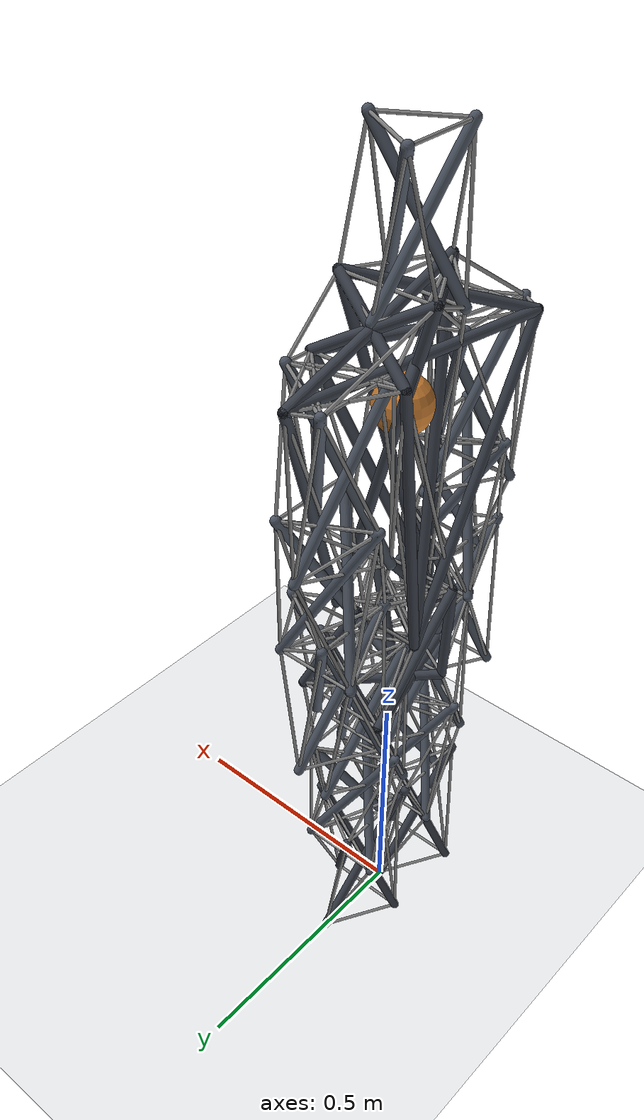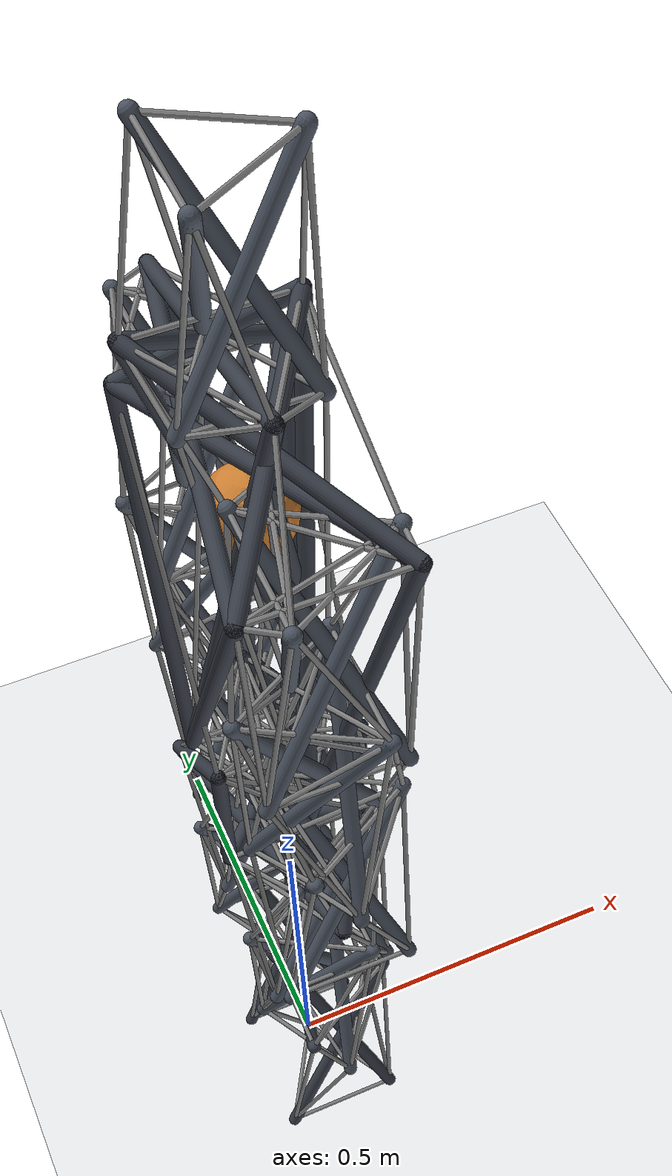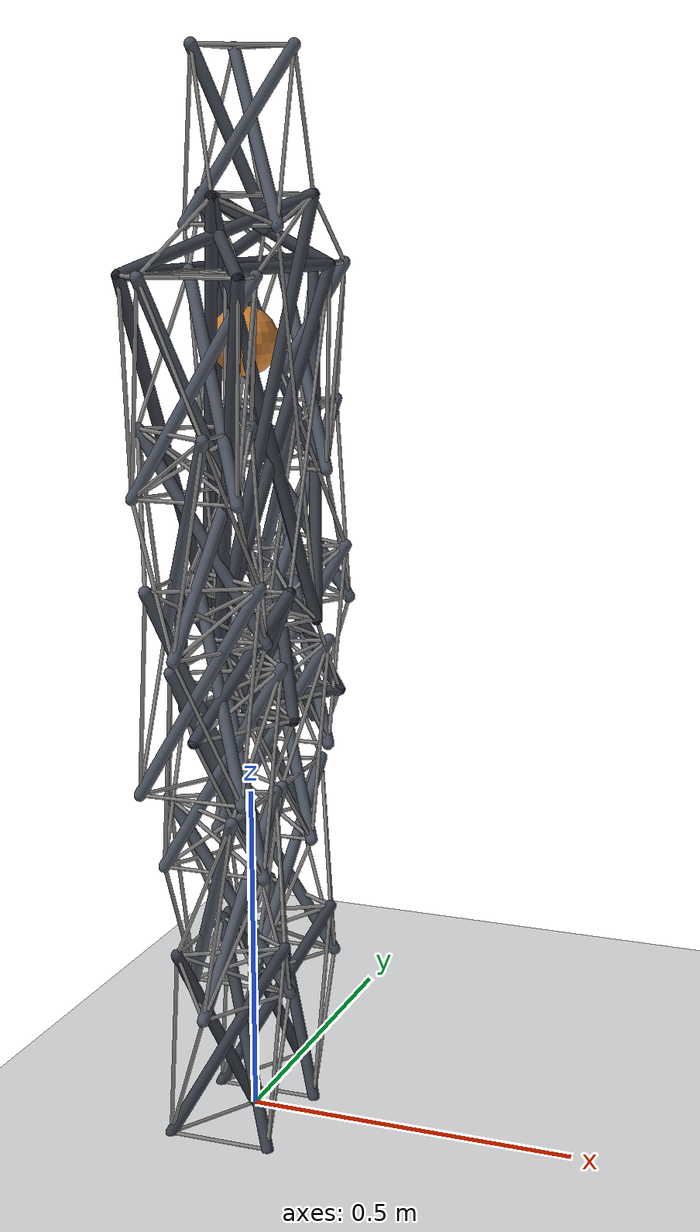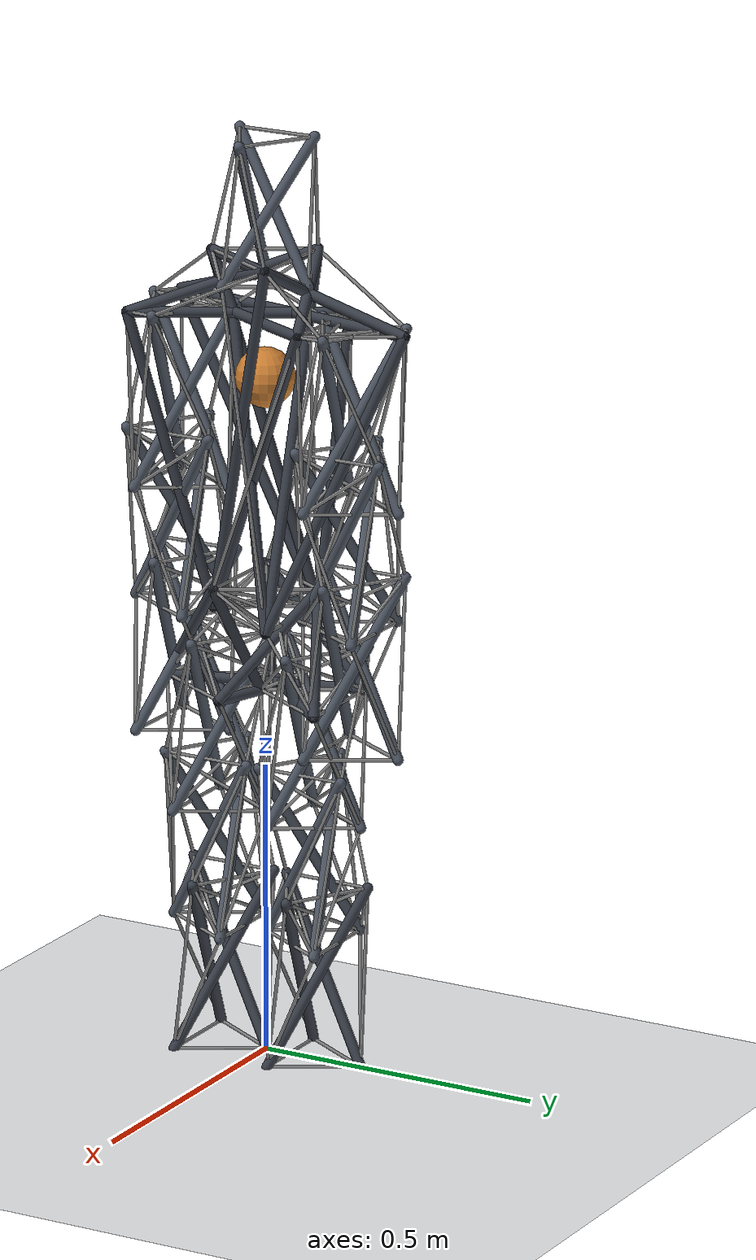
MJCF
<mujoco model="cell_graph">
  <compiler angle="radian" autolimits="true"/>
  <visual>
    <global offwidth="1600" offheight="1200"/>
    <headlight diffuse="0.7 0.7 0.7" ambient="0.45 0.45 0.45"
               specular="0.1 0.1 0.1"/>
  </visual>
  <asset>
    <texture type="skybox" builtin="flat" rgb1="1 1 1" rgb2="1 1 1"
             width="256" height="256"/>
    <texture name="grid" type="2d" builtin="checker" rgb1="0.88 0.89 0.90"
             rgb2="0.96 0.96 0.97" width="512" height="512"/>
    <material name="grid" texture="grid" texrepeat="10 10" reflectance="0.05"/>
  </asset>
  <option timestep="5e-05" integrator="implicitfast" gravity="0 0 -9.81"/>
  <worldbody>
    <light pos="1.2 -1.2 2.6" dir="-0.4 0.4 -1" directional="true"
           diffuse="0.85 0.85 0.85"/>
    <light pos="-1.5 1.0 2.0" dir="0.5 -0.35 -1" directional="true"
           diffuse="0.35 0.35 0.35"/>
    <geom name="floor" type="plane" size="4 4 0.1" material="grid"
          contype="0" conaffinity="0"/>
    <geom type="capsule" size="0.009" contype="0" conaffinity="0" rgba="0.22 0.24 0.28 1" fromto="0.00000 0.18000 0.00000 -0.04527 0.01222 0.30000"/>
    <geom type="capsule" size="0.009" contype="0" conaffinity="0" rgba="0.22 0.24 0.28 1" fromto="-0.07794 0.04500 0.00000 0.09000 0.08969 0.30000"/>
    <geom type="capsule" size="0.009" contype="0" conaffinity="0" rgba="0.22 0.24 0.28 1" fromto="0.07794 0.04500 0.00000 -0.04473 0.16810 0.30000"/>
    <geom type="capsule" size="0.009" contype="0" conaffinity="0" rgba="0.22 0.24 0.28 1" fromto="0.00000 0.00000 0.00000 -0.04527 -0.16778 0.30000"/>
    <geom type="capsule" size="0.009" contype="0" conaffinity="0" rgba="0.22 0.24 0.28 1" fromto="-0.07794 -0.13500 0.00000 0.09000 -0.09031 0.30000"/>
    <geom type="capsule" size="0.009" contype="0" conaffinity="0" rgba="0.22 0.24 0.28 1" fromto="0.07794 -0.13500 0.00000 -0.04473 -0.01190 0.30000"/>
    <site name="legl0_b0" pos="0.00000 0.18000 0.00000" size="0.005"/>
    <site name="legl0_t0" pos="-0.04473 0.16810 0.30000" size="0.005"/>
    <site name="legl0_b1" pos="-0.07794 0.04500 0.00000" size="0.005"/>
    <site name="legl0_t1" pos="-0.04527 0.01222 0.30000" size="0.005"/>
    <site name="legl0_b2" pos="0.07794 0.04500 0.00000" size="0.005"/>
    <site name="legl0_t2" pos="0.09000 0.08969 0.30000" size="0.005"/>
    <site name="legr0_b0" pos="0.00000 0.00000 0.00000" size="0.005"/>
    <site name="legr0_t0" pos="-0.04473 -0.01190 0.30000" size="0.005"/>
    <site name="legr0_b1" pos="-0.07794 -0.13500 0.00000" size="0.005"/>
    <site name="legr0_t1" pos="-0.04527 -0.16778 0.30000" size="0.005"/>
    <site name="legr0_b2" pos="0.07794 -0.13500 0.00000" size="0.005"/>
    <site name="legr0_t2" pos="0.09000 -0.09031 0.30000" size="0.005"/>

    <body name="legl1_s0" pos="-0.01661 0.07345 0.36000">
      <freejoint/>
      <geom type="capsule" size="0.009" mass="0.0200"
            contype="0" conaffinity="0" rgba="0.30 0.33 0.38 1"
            fromto="-0.06133 0.06155 -0.15000
                    0.06133 -0.06155 0.15000"/>      <site name="legl1_b0" pos="-0.06133 0.06155 -0.15000" size="0.005"/>      <site name="legl1_t1" pos="0.06133 -0.06155 0.15000" size="0.005"/>    </body>
    <body name="legl1_s1" pos="0.02264 0.08389 0.36000">
      <freejoint/>
      <geom type="capsule" size="0.009" mass="0.0200"
            contype="0" conaffinity="0" rgba="0.30 0.33 0.38 1"
            fromto="-0.02264 -0.08389 -0.15000
                    0.02264 0.08389 0.15000"/>      <site name="legl1_b1" pos="-0.02264 -0.08389 -0.15000" size="0.005"/>      <site name="legl1_t2" pos="0.02264 0.08389 0.15000" size="0.005"/>    </body>
    <body name="legl1_s2" pos="-0.00603 0.11266 0.36000">
      <freejoint/>
      <geom type="capsule" size="0.009" mass="0.0200"
            contype="0" conaffinity="0" rgba="0.30 0.33 0.38 1"
            fromto="0.08397 0.02234 -0.15000
                    -0.08397 -0.02234 0.15000"/>      <site name="legl1_b2" pos="0.08397 0.02234 -0.15000" size="0.005"/>      <site name="legl1_t0" pos="-0.08397 -0.02234 0.15000" size="0.005"/>    </body>
    <body name="legl2_s0" pos="0.00603 0.06734 0.57000">
      <freejoint/>
      <geom type="capsule" size="0.009" mass="0.0200"
            contype="0" conaffinity="0" rgba="0.30 0.33 0.38 1"
            fromto="-0.08397 -0.02234 -0.15000
                    0.08397 0.02234 0.15000"/>      <site name="legl2_b0" pos="-0.08397 -0.02234 -0.15000" size="0.005"/>      <site name="legl2_t1" pos="0.08397 0.02234 0.15000" size="0.005"/>    </body>
    <body name="legl2_s1" pos="0.01661 0.10655 0.57000">
      <freejoint/>
      <geom type="capsule" size="0.009" mass="0.0200"
            contype="0" conaffinity="0" rgba="0.30 0.33 0.38 1"
            fromto="0.06133 -0.06155 -0.15000
                    -0.06133 0.06155 0.15000"/>      <site name="legl2_b1" pos="0.06133 -0.06155 -0.15000" size="0.005"/>      <site name="legl2_t2" pos="-0.06133 0.06155 0.15000" size="0.005"/>    </body>
    <body name="legl2_s2" pos="-0.02264 0.09611 0.57000">
      <freejoint/>
      <geom type="capsule" size="0.009" mass="0.0200"
            contype="0" conaffinity="0" rgba="0.30 0.33 0.38 1"
            fromto="0.02264 0.08389 -0.15000
                    -0.02264 -0.08389 0.15000"/>      <site name="legl2_b2" pos="0.02264 0.08389 -0.15000" size="0.005"/>      <site name="legl2_t0" pos="-0.02264 -0.08389 0.15000" size="0.005"/>    </body>
    <body name="legr1_s0" pos="-0.01661 -0.10655 0.36000">
      <freejoint/>
      <geom type="capsule" size="0.009" mass="0.0200"
            contype="0" conaffinity="0" rgba="0.30 0.33 0.38 1"
            fromto="-0.06133 0.06155 -0.15000
                    0.06133 -0.06155 0.15000"/>      <site name="legr1_b0" pos="-0.06133 0.06155 -0.15000" size="0.005"/>      <site name="legr1_t1" pos="0.06133 -0.06155 0.15000" size="0.005"/>    </body>
    <body name="legr1_s1" pos="0.02264 -0.09611 0.36000">
      <freejoint/>
      <geom type="capsule" size="0.009" mass="0.0200"
            contype="0" conaffinity="0" rgba="0.30 0.33 0.38 1"
            fromto="-0.02264 -0.08389 -0.15000
                    0.02264 0.08389 0.15000"/>      <site name="legr1_b1" pos="-0.02264 -0.08389 -0.15000" size="0.005"/>      <site name="legr1_t2" pos="0.02264 0.08389 0.15000" size="0.005"/>    </body>
    <body name="legr1_s2" pos="-0.00603 -0.06734 0.36000">
      <freejoint/>
      <geom type="capsule" size="0.009" mass="0.0200"
            contype="0" conaffinity="0" rgba="0.30 0.33 0.38 1"
            fromto="0.08397 0.02234 -0.15000
                    -0.08397 -0.02234 0.15000"/>      <site name="legr1_b2" pos="0.08397 0.02234 -0.15000" size="0.005"/>      <site name="legr1_t0" pos="-0.08397 -0.02234 0.15000" size="0.005"/>    </body>
    <body name="legr2_s0" pos="0.00603 -0.11266 0.57000">
      <freejoint/>
      <geom type="capsule" size="0.009" mass="0.0200"
            contype="0" conaffinity="0" rgba="0.30 0.33 0.38 1"
            fromto="-0.08397 -0.02234 -0.15000
                    0.08397 0.02234 0.15000"/>      <site name="legr2_b0" pos="-0.08397 -0.02234 -0.15000" size="0.005"/>      <site name="legr2_t1" pos="0.08397 0.02234 0.15000" size="0.005"/>    </body>
    <body name="legr2_s1" pos="0.01661 -0.07345 0.57000">
      <freejoint/>
      <geom type="capsule" size="0.009" mass="0.0200"
            contype="0" conaffinity="0" rgba="0.30 0.33 0.38 1"
            fromto="0.06133 -0.06155 -0.15000
                    -0.06133 0.06155 0.15000"/>      <site name="legr2_b1" pos="0.06133 -0.06155 -0.15000" size="0.005"/>      <site name="legr2_t2" pos="-0.06133 0.06155 0.15000" size="0.005"/>    </body>
    <body name="legr2_s2" pos="-0.02264 -0.08389 0.57000">
      <freejoint/>
      <geom type="capsule" size="0.009" mass="0.0200"
            contype="0" conaffinity="0" rgba="0.30 0.33 0.38 1"
            fromto="0.02264 0.08389 -0.15000
                    -0.02264 -0.08389 0.15000"/>      <site name="legr2_b2" pos="0.02264 0.08389 -0.15000" size="0.005"/>      <site name="legr2_t0" pos="-0.02264 -0.08389 0.15000" size="0.005"/>    </body>
    <body name="arml0_s0" pos="-0.02264 0.16611 1.12000">
      <freejoint/>
      <geom type="capsule" size="0.009" mass="0.0200"
            contype="0" conaffinity="0" rgba="0.30 0.33 0.38 1"
            fromto="0.02264 0.08389 -0.15000
                    -0.02264 -0.08389 0.15000"/>      <site name="arml0_b0" pos="0.02264 0.08389 -0.15000" size="0.005"/>      <site name="arml0_t1" pos="-0.02264 -0.08389 0.15000" size="0.005"/>    </body>
    <body name="arml0_s1" pos="0.00603 0.13734 1.12000">
      <freejoint/>
      <geom type="capsule" size="0.009" mass="0.0200"
            contype="0" conaffinity="0" rgba="0.30 0.33 0.38 1"
            fromto="-0.08397 -0.02234 -0.15000
                    0.08397 0.02234 0.15000"/>      <site name="arml0_b1" pos="-0.08397 -0.02234 -0.15000" size="0.005"/>      <site name="arml0_t2" pos="0.08397 0.02234 0.15000" size="0.005"/>    </body>
    <body name="arml0_s2" pos="0.01661 0.17655 1.12000">
      <freejoint/>
      <geom type="capsule" size="0.009" mass="0.0200"
            contype="0" conaffinity="0" rgba="0.30 0.33 0.38 1"
            fromto="0.06133 -0.06155 -0.15000
                    -0.06133 0.06155 0.15000"/>      <site name="arml0_b2" pos="0.06133 -0.06155 -0.15000" size="0.005"/>      <site name="arml0_t0" pos="-0.06133 0.06155 0.15000" size="0.005"/>    </body>
    <body name="arml1_s0" pos="-0.01661 0.14345 0.91000">
      <freejoint/>
      <geom type="capsule" size="0.009" mass="0.0200"
            contype="0" conaffinity="0" rgba="0.30 0.33 0.38 1"
            fromto="-0.06133 0.06155 -0.15000
                    0.06133 -0.06155 0.15000"/>      <site name="arml1_b0" pos="-0.06133 0.06155 -0.15000" size="0.005"/>      <site name="arml1_t1" pos="0.06133 -0.06155 0.15000" size="0.005"/>    </body>
    <body name="arml1_s1" pos="0.02264 0.15389 0.91000">
      <freejoint/>
      <geom type="capsule" size="0.009" mass="0.0200"
            contype="0" conaffinity="0" rgba="0.30 0.33 0.38 1"
            fromto="-0.02264 -0.08389 -0.15000
                    0.02264 0.08389 0.15000"/>      <site name="arml1_b1" pos="-0.02264 -0.08389 -0.15000" size="0.005"/>      <site name="arml1_t2" pos="0.02264 0.08389 0.15000" size="0.005"/>    </body>
    <body name="arml1_s2" pos="-0.00603 0.18266 0.91000">
      <freejoint/>
      <geom type="capsule" size="0.009" mass="0.0200"
            contype="0" conaffinity="0" rgba="0.30 0.33 0.38 1"
            fromto="0.08397 0.02234 -0.15000
                    -0.08397 -0.02234 0.15000"/>      <site name="arml1_b2" pos="0.08397 0.02234 -0.15000" size="0.005"/>      <site name="arml1_t0" pos="-0.08397 -0.02234 0.15000" size="0.005"/>    </body>
    <body name="arml2_s0" pos="0.00603 0.13734 0.70000">
      <freejoint/>
      <geom type="capsule" size="0.009" mass="0.0200"
            contype="0" conaffinity="0" rgba="0.30 0.33 0.38 1"
            fromto="-0.08397 -0.02234 -0.15000
                    0.08397 0.02234 0.15000"/>      <site name="arml2_b0" pos="-0.08397 -0.02234 -0.15000" size="0.005"/>      <site name="arml2_t1" pos="0.08397 0.02234 0.15000" size="0.005"/>    </body>
    <body name="arml2_s1" pos="0.01661 0.17655 0.70000">
      <freejoint/>
      <geom type="capsule" size="0.009" mass="0.0200"
            contype="0" conaffinity="0" rgba="0.30 0.33 0.38 1"
            fromto="0.06133 -0.06155 -0.15000
                    -0.06133 0.06155 0.15000"/>      <site name="arml2_b1" pos="0.06133 -0.06155 -0.15000" size="0.005"/>      <site name="arml2_t2" pos="-0.06133 0.06155 0.15000" size="0.005"/>    </body>
    <body name="arml2_s2" pos="-0.02264 0.16611 0.70000">
      <freejoint/>
      <geom type="capsule" size="0.009" mass="0.0200"
            contype="0" conaffinity="0" rgba="0.30 0.33 0.38 1"
            fromto="0.02264 0.08389 -0.15000
                    -0.02264 -0.08389 0.15000"/>      <site name="arml2_b2" pos="0.02264 0.08389 -0.15000" size="0.005"/>      <site name="arml2_t0" pos="-0.02264 -0.08389 0.15000" size="0.005"/>    </body>
    <body name="armr0_s0" pos="-0.02264 -0.15389 1.12000">
      <freejoint/>
      <geom type="capsule" size="0.009" mass="0.0200"
            contype="0" conaffinity="0" rgba="0.30 0.33 0.38 1"
            fromto="0.02264 0.08389 -0.15000
                    -0.02264 -0.08389 0.15000"/>      <site name="armr0_b0" pos="0.02264 0.08389 -0.15000" size="0.005"/>      <site name="armr0_t1" pos="-0.02264 -0.08389 0.15000" size="0.005"/>    </body>
    <body name="armr0_s1" pos="0.00603 -0.18266 1.12000">
      <freejoint/>
      <geom type="capsule" size="0.009" mass="0.0200"
            contype="0" conaffinity="0" rgba="0.30 0.33 0.38 1"
            fromto="-0.08397 -0.02234 -0.15000
                    0.08397 0.02234 0.15000"/>      <site name="armr0_b1" pos="-0.08397 -0.02234 -0.15000" size="0.005"/>      <site name="armr0_t2" pos="0.08397 0.02234 0.15000" size="0.005"/>    </body>
    <body name="armr0_s2" pos="0.01661 -0.14345 1.12000">
      <freejoint/>
      <geom type="capsule" size="0.009" mass="0.0200"
            contype="0" conaffinity="0" rgba="0.30 0.33 0.38 1"
            fromto="0.06133 -0.06155 -0.15000
                    -0.06133 0.06155 0.15000"/>      <site name="armr0_b2" pos="0.06133 -0.06155 -0.15000" size="0.005"/>      <site name="armr0_t0" pos="-0.06133 0.06155 0.15000" size="0.005"/>    </body>
    <body name="armr1_s0" pos="-0.01661 -0.17655 0.91000">
      <freejoint/>
      <geom type="capsule" size="0.009" mass="0.0200"
            contype="0" conaffinity="0" rgba="0.30 0.33 0.38 1"
            fromto="-0.06133 0.06155 -0.15000
                    0.06133 -0.06155 0.15000"/>      <site name="armr1_b0" pos="-0.06133 0.06155 -0.15000" size="0.005"/>      <site name="armr1_t1" pos="0.06133 -0.06155 0.15000" size="0.005"/>    </body>
    <body name="armr1_s1" pos="0.02264 -0.16611 0.91000">
      <freejoint/>
      <geom type="capsule" size="0.009" mass="0.0200"
            contype="0" conaffinity="0" rgba="0.30 0.33 0.38 1"
            fromto="-0.02264 -0.08389 -0.15000
                    0.02264 0.08389 0.15000"/>      <site name="armr1_b1" pos="-0.02264 -0.08389 -0.15000" size="0.005"/>      <site name="armr1_t2" pos="0.02264 0.08389 0.15000" size="0.005"/>    </body>
    <body name="armr1_s2" pos="-0.00603 -0.13734 0.91000">
      <freejoint/>
      <geom type="capsule" size="0.009" mass="0.0200"
            contype="0" conaffinity="0" rgba="0.30 0.33 0.38 1"
            fromto="0.08397 0.02234 -0.15000
                    -0.08397 -0.02234 0.15000"/>      <site name="armr1_b2" pos="0.08397 0.02234 -0.15000" size="0.005"/>      <site name="armr1_t0" pos="-0.08397 -0.02234 0.15000" size="0.005"/>    </body>
    <body name="armr2_s0" pos="0.00603 -0.18266 0.70000">
      <freejoint/>
      <geom type="capsule" size="0.009" mass="0.0200"
            contype="0" conaffinity="0" rgba="0.30 0.33 0.38 1"
            fromto="-0.08397 -0.02234 -0.15000
                    0.08397 0.02234 0.15000"/>      <site name="armr2_b0" pos="-0.08397 -0.02234 -0.15000" size="0.005"/>      <site name="armr2_t1" pos="0.08397 0.02234 0.15000" size="0.005"/>    </body>
    <body name="armr2_s1" pos="0.01661 -0.14345 0.70000">
      <freejoint/>
      <geom type="capsule" size="0.009" mass="0.0200"
            contype="0" conaffinity="0" rgba="0.30 0.33 0.38 1"
            fromto="0.06133 -0.06155 -0.15000
                    -0.06133 0.06155 0.15000"/>      <site name="armr2_b1" pos="0.06133 -0.06155 -0.15000" size="0.005"/>      <site name="armr2_t2" pos="-0.06133 0.06155 0.15000" size="0.005"/>    </body>
    <body name="armr2_s2" pos="-0.02264 -0.15389 0.70000">
      <freejoint/>
      <geom type="capsule" size="0.009" mass="0.0200"
            contype="0" conaffinity="0" rgba="0.30 0.33 0.38 1"
            fromto="0.02264 0.08389 -0.15000
                    -0.02264 -0.08389 0.15000"/>      <site name="armr2_b2" pos="0.02264 0.08389 -0.15000" size="0.005"/>      <site name="armr2_t0" pos="-0.02264 -0.08389 0.15000" size="0.005"/>    </body>
    <body name="head_s0" pos="-0.02037 0.00550 1.45000">
      <freejoint/>
      <geom type="capsule" size="0.009" mass="0.0200"
            contype="0" conaffinity="0" rgba="0.30 0.33 0.38 1"
            fromto="0.02037 0.07550 -0.12000
                    -0.02037 -0.07550 0.12000"/>      <site name="head_b0" pos="0.02037 0.07550 -0.12000" size="0.005"/>      <site name="head_t1" pos="-0.02037 -0.07550 0.12000" size="0.005"/>    </body>
    <body name="head_s1" pos="0.00543 -0.02039 1.45000">
      <freejoint/>
      <geom type="capsule" size="0.009" mass="0.0200"
            contype="0" conaffinity="0" rgba="0.30 0.33 0.38 1"
            fromto="-0.07557 -0.02011 -0.12000
                    0.07557 0.02011 0.12000"/>      <site name="head_b1" pos="-0.07557 -0.02011 -0.12000" size="0.005"/>      <site name="head_t2" pos="0.07557 0.02011 0.12000" size="0.005"/>    </body>
    <body name="head_s2" pos="0.01495 0.01489 1.45000">
      <freejoint/>
      <geom type="capsule" size="0.009" mass="0.0200"
            contype="0" conaffinity="0" rgba="0.30 0.33 0.38 1"
            fromto="0.05520 -0.05539 -0.12000
                    -0.05520 0.05539 0.12000"/>      <site name="head_b2" pos="0.05520 -0.05539 -0.12000" size="0.005"/>      <site name="head_t0" pos="-0.05520 0.05539 0.12000" size="0.005"/>    </body>
    <body name="pel" pos="0.00000 -0.00000 0.69333">
      <freejoint/>
      <geom type="capsule" size="0.009" mass="0.0200" contype="0" conaffinity="0" rgba="0.22 0.24 0.28 1" fromto="-0.08660 0.14000 -0.06333 -0.00000 -0.19000 -0.06333"/>
      <geom type="capsule" size="0.009" mass="0.0200" contype="0" conaffinity="0" rgba="0.22 0.24 0.28 1" fromto="-0.00000 -0.01000 -0.06333 0.08660 -0.04000 -0.06333"/>
      <geom type="capsule" size="0.009" mass="0.0200" contype="0" conaffinity="0" rgba="0.22 0.24 0.28 1" fromto="0.08660 0.14000 -0.06333 -0.08660 -0.04000 -0.06333"/>
      <geom type="capsule" size="0.009" mass="0.0200" contype="0" conaffinity="0" rgba="0.22 0.24 0.28 1" fromto="-0.08660 0.14000 -0.06333 -0.08660 -0.05000 0.12667"/>
      <geom type="capsule" size="0.009" mass="0.0200" contype="0" conaffinity="0" rgba="0.22 0.24 0.28 1" fromto="-0.00000 -0.01000 -0.06333 0.08660 -0.05000 0.12667"/>
      <geom type="capsule" size="0.009" mass="0.0200" contype="0" conaffinity="0" rgba="0.22 0.24 0.28 1" fromto="0.08660 0.14000 -0.06333 -0.00000 0.10000 0.12667"/>
      <geom type="capsule" size="0.009" mass="0.0200" contype="0" conaffinity="0" rgba="0.22 0.24 0.28 1" fromto="-0.08660 -0.04000 -0.06333 -0.08660 -0.05000 0.12667"/>
      <geom type="capsule" size="0.009" mass="0.0200" contype="0" conaffinity="0" rgba="0.22 0.24 0.28 1" fromto="-0.00000 -0.19000 -0.06333 0.08660 -0.05000 0.12667"/>
      <geom type="capsule" size="0.009" mass="0.0200" contype="0" conaffinity="0" rgba="0.22 0.24 0.28 1" fromto="0.08660 -0.04000 -0.06333 -0.00000 0.10000 0.12667"/>
      <site name="pel_hipl0" pos="-0.08660 0.14000 -0.06333" size="0.005"/>
      <site name="pel_hipl1" pos="-0.00000 -0.01000 -0.06333" size="0.005"/>
      <site name="pel_hipl2" pos="0.08660 0.14000 -0.06333" size="0.005"/>
      <site name="pel_hipr0" pos="-0.08660 -0.04000 -0.06333" size="0.005"/>
      <site name="pel_hipr1" pos="-0.00000 -0.19000 -0.06333" size="0.005"/>
      <site name="pel_hipr2" pos="0.08660 -0.04000 -0.06333" size="0.005"/>
      <site name="pel_waist0" pos="-0.00000 0.10000 0.12667" size="0.005"/>
      <site name="pel_waist1" pos="-0.08660 -0.05000 0.12667" size="0.005"/>
      <site name="pel_waist2" pos="0.08660 -0.05000 0.12667" size="0.005"/>
    </body>
    <body name="tor" pos="-0.00000 -0.00000 1.16750">
      <freejoint/>
      <geom type="capsule" size="0.009" mass="0.0226" contype="0" conaffinity="0" rgba="0.22 0.24 0.28 1" fromto="-0.08660 0.05000 -0.40750 -0.08660 0.11000 0.10250"/>
      <geom type="capsule" size="0.009" mass="0.0246" contype="0" conaffinity="0" rgba="0.22 0.24 0.28 1" fromto="-0.00000 -0.10000 -0.40750 0.08660 0.11000 0.10250"/>
      <geom type="capsule" size="0.009" mass="0.0246" contype="0" conaffinity="0" rgba="0.22 0.24 0.28 1" fromto="0.08660 0.05000 -0.40750 0.00000 0.26000 0.10250"/>
      <geom type="capsule" size="0.009" mass="0.0252" contype="0" conaffinity="0" rgba="0.22 0.24 0.28 1" fromto="-0.08660 0.05000 -0.40750 -0.08660 -0.21000 0.10250"/>
      <geom type="capsule" size="0.009" mass="0.0233" contype="0" conaffinity="0" rgba="0.22 0.24 0.28 1" fromto="-0.00000 -0.10000 -0.40750 0.08660 -0.21000 0.10250"/>
      <geom type="capsule" size="0.009" mass="0.0233" contype="0" conaffinity="0" rgba="0.22 0.24 0.28 1" fromto="0.08660 0.05000 -0.40750 0.00000 -0.06000 0.10250"/>
      <geom type="capsule" size="0.009" mass="0.0279" contype="0" conaffinity="0" rgba="0.22 0.24 0.28 1" fromto="-0.08660 0.05000 -0.40750 -0.00000 -0.10000 0.20250"/>
      <geom type="capsule" size="0.009" mass="0.0279" contype="0" conaffinity="0" rgba="0.22 0.24 0.28 1" fromto="-0.00000 -0.10000 -0.40750 0.08660 0.05000 0.20250"/>
      <geom type="capsule" size="0.009" mass="0.0279" contype="0" conaffinity="0" rgba="0.22 0.24 0.28 1" fromto="0.08660 0.05000 -0.40750 -0.08660 0.05000 0.20250"/>
      <geom type="capsule" size="0.009" mass="0.0210" contype="0" conaffinity="0" rgba="0.22 0.24 0.28 1" fromto="0.00000 0.26000 0.10250 -0.08660 -0.21000 0.10250"/>
      <geom type="capsule" size="0.009" mass="0.0200" contype="0" conaffinity="0" rgba="0.22 0.24 0.28 1" fromto="-0.08660 0.11000 0.10250 0.08660 -0.21000 0.10250"/>
      <geom type="capsule" size="0.009" mass="0.0200" contype="0" conaffinity="0" rgba="0.22 0.24 0.28 1" fromto="0.08660 0.11000 0.10250 0.00000 -0.06000 0.10250"/>
      <geom type="capsule" size="0.009" mass="0.0200" contype="0" conaffinity="0" rgba="0.22 0.24 0.28 1" fromto="0.00000 0.26000 0.10250 -0.00000 -0.10000 0.20250"/>
      <geom type="capsule" size="0.009" mass="0.0200" contype="0" conaffinity="0" rgba="0.22 0.24 0.28 1" fromto="-0.08660 0.11000 0.10250 0.08660 0.05000 0.20250"/>
      <geom type="capsule" size="0.009" mass="0.0200" contype="0" conaffinity="0" rgba="0.22 0.24 0.28 1" fromto="0.08660 0.11000 0.10250 -0.08660 0.05000 0.20250"/>
      <geom type="capsule" size="0.009" mass="0.0200" contype="0" conaffinity="0" rgba="0.22 0.24 0.28 1" fromto="0.00000 -0.06000 0.10250 -0.00000 -0.10000 0.20250"/>
      <geom type="capsule" size="0.009" mass="0.0200" contype="0" conaffinity="0" rgba="0.22 0.24 0.28 1" fromto="-0.08660 -0.21000 0.10250 0.08660 0.05000 0.20250"/>
      <geom type="capsule" size="0.009" mass="0.0200" contype="0" conaffinity="0" rgba="0.22 0.24 0.28 1" fromto="0.08660 -0.21000 0.10250 -0.08660 0.05000 0.20250"/>
      <site name="tor_waist0" pos="-0.08660 0.05000 -0.40750" size="0.005"/>
      <site name="tor_waist1" pos="-0.00000 -0.10000 -0.40750" size="0.005"/>
      <site name="tor_waist2" pos="0.08660 0.05000 -0.40750" size="0.005"/>
      <site name="tor_shl0" pos="0.00000 0.26000 0.10250" size="0.005"/>
      <site name="tor_shl1" pos="-0.08660 0.11000 0.10250" size="0.005"/>
      <site name="tor_shl2" pos="0.08660 0.11000 0.10250" size="0.005"/>
      <site name="tor_shr0" pos="0.00000 -0.06000 0.10250" size="0.005"/>
      <site name="tor_shr1" pos="-0.08660 -0.21000 0.10250" size="0.005"/>
      <site name="tor_shr2" pos="0.08660 -0.21000 0.10250" size="0.005"/>
      <site name="tor_neck0" pos="-0.08660 0.05000 0.20250" size="0.005"/>
      <site name="tor_neck1" pos="-0.00000 -0.10000 0.20250" size="0.005"/>
      <site name="tor_neck2" pos="0.08660 0.05000 0.20250" size="0.005"/>
      <geom type="sphere" size="0.05" mass="22.0" contype="0" conaffinity="0" rgba="0.8 0.5 0.2 1" pos="0 0 0"/>
    </body>
  </worldbody>
  <tendon>
    <spatial name="c0" width="0.003" stiffness="40000.0" damping="4.00" springlength="0 0.130883">
      <site site="legl0_b0"/>
      <site site="legl0_b1"/>
    </spatial>
    <spatial name="c1" width="0.003" stiffness="40000.0" damping="4.00" springlength="0 0.130881">
      <site site="legl0_t0"/>
      <site site="legl0_t1"/>
    </spatial>
    <spatial name="c2" width="0.003" stiffness="40000.0" damping="4.00" springlength="0 0.278550">
      <site site="legl0_b0"/>
      <site site="legl0_t0"/>
    </spatial>
    <spatial name="c3" width="0.003" stiffness="40000.0" damping="4.00" springlength="0 0.130880">
      <site site="legl0_b1"/>
      <site site="legl0_b2"/>
    </spatial>
    <spatial name="c4" width="0.003" stiffness="40000.0" damping="4.00" springlength="0 0.130883">
      <site site="legl0_t1"/>
      <site site="legl0_t2"/>
    </spatial>
    <spatial name="c5" width="0.003" stiffness="40000.0" damping="4.00" springlength="0 0.278549">
      <site site="legl0_b1"/>
      <site site="legl0_t1"/>
    </spatial>
    <spatial name="c6" width="0.003" stiffness="40000.0" damping="4.00" springlength="0 0.130883">
      <site site="legl0_b2"/>
      <site site="legl0_b0"/>
    </spatial>
    <spatial name="c7" width="0.003" stiffness="40000.0" damping="4.00" springlength="0 0.130886">
      <site site="legl0_t2"/>
      <site site="legl0_t0"/>
    </spatial>
    <spatial name="c8" width="0.003" stiffness="40000.0" damping="4.00" springlength="0 0.278550">
      <site site="legl0_b2"/>
      <site site="legl0_t2"/>
    </spatial>
    <spatial name="c9" width="0.003" stiffness="40000.0" damping="4.00" springlength="0 0.130883">
      <site site="legl1_b0"/>
      <site site="legl1_b1"/>
    </spatial>
    <spatial name="c10" width="0.003" stiffness="40000.0" damping="4.00" springlength="0 0.130882">
      <site site="legl1_t0"/>
      <site site="legl1_t1"/>
    </spatial>
    <spatial name="c11" width="0.003" stiffness="40000.0" damping="4.00" springlength="0 0.278549">
      <site site="legl1_b0"/>
      <site site="legl1_t0"/>
    </spatial>
    <spatial name="c12" width="0.003" stiffness="40000.0" damping="4.00" springlength="0 0.130883">
      <site site="legl1_b1"/>
      <site site="legl1_b2"/>
    </spatial>
    <spatial name="c13" width="0.003" stiffness="40000.0" damping="4.00" springlength="0 0.130881">
      <site site="legl1_t1"/>
      <site site="legl1_t2"/>
    </spatial>
    <spatial name="c14" width="0.003" stiffness="40000.0" damping="4.00" springlength="0 0.278548">
      <site site="legl1_b1"/>
      <site site="legl1_t1"/>
    </spatial>
    <spatial name="c15" width="0.003" stiffness="40000.0" damping="4.00" springlength="0 0.130880">
      <site site="legl1_b2"/>
      <site site="legl1_b0"/>
    </spatial>
    <spatial name="c16" width="0.003" stiffness="40000.0" damping="4.00" springlength="0 0.130887">
      <site site="legl1_t2"/>
      <site site="legl1_t0"/>
    </spatial>
    <spatial name="c17" width="0.003" stiffness="40000.0" damping="4.00" springlength="0 0.278548">
      <site site="legl1_b2"/>
      <site site="legl1_t2"/>
    </spatial>
    <spatial name="c18" width="0.003" stiffness="40000.0" damping="4.00" springlength="0 0.076482">
      <site site="legl0_t0"/>
      <site site="legl1_b0"/>
    </spatial>
    <spatial name="c19" width="0.003" stiffness="40000.0" damping="4.00" springlength="0 0.203471">
      <site site="legl0_t0"/>
      <site site="legl1_t0"/>
    </spatial>
    <spatial name="c20" width="0.003" stiffness="40000.0" damping="4.00" springlength="0 0.170853">
      <site site="legl0_t0"/>
      <site site="legl1_b1"/>
    </spatial>
    <spatial name="c21" width="0.003" stiffness="40000.0" damping="4.00" springlength="0 0.203472">
      <site site="legl0_b0"/>
      <site site="legl1_b0"/>
    </spatial>
    <spatial name="c22" width="0.003" stiffness="40000.0" damping="4.00" springlength="0 0.076483">
      <site site="legl0_t1"/>
      <site site="legl1_b1"/>
    </spatial>
    <spatial name="c23" width="0.003" stiffness="40000.0" damping="4.00" springlength="0 0.203469">
      <site site="legl0_t1"/>
      <site site="legl1_t1"/>
    </spatial>
    <spatial name="c24" width="0.003" stiffness="40000.0" damping="4.00" springlength="0 0.170846">
      <site site="legl0_t1"/>
      <site site="legl1_b2"/>
    </spatial>
    <spatial name="c25" width="0.003" stiffness="40000.0" damping="4.00" springlength="0 0.203472">
      <site site="legl0_b1"/>
      <site site="legl1_b1"/>
    </spatial>
    <spatial name="c26" width="0.003" stiffness="40000.0" damping="4.00" springlength="0 0.076481">
      <site site="legl0_t2"/>
      <site site="legl1_b2"/>
    </spatial>
    <spatial name="c27" width="0.003" stiffness="40000.0" damping="4.00" springlength="0 0.203469">
      <site site="legl0_t2"/>
      <site site="legl1_t2"/>
    </spatial>
    <spatial name="c28" width="0.003" stiffness="40000.0" damping="4.00" springlength="0 0.170849">
      <site site="legl0_t2"/>
      <site site="legl1_b0"/>
    </spatial>
    <spatial name="c29" width="0.003" stiffness="40000.0" damping="4.00" springlength="0 0.203473">
      <site site="legl0_b2"/>
      <site site="legl1_b2"/>
    </spatial>
    <spatial name="c30" width="0.003" stiffness="40000.0" damping="4.00" springlength="0 0.130880">
      <site site="legl2_b0"/>
      <site site="legl2_b1"/>
    </spatial>
    <spatial name="c31" width="0.003" stiffness="40000.0" damping="4.00" springlength="0 0.130887">
      <site site="legl2_t0"/>
      <site site="legl2_t1"/>
    </spatial>
    <spatial name="c32" width="0.003" stiffness="40000.0" damping="4.00" springlength="0 0.278548">
      <site site="legl2_b0"/>
      <site site="legl2_t0"/>
    </spatial>
    <spatial name="c33" width="0.003" stiffness="40000.0" damping="4.00" springlength="0 0.130883">
      <site site="legl2_b1"/>
      <site site="legl2_b2"/>
    </spatial>
    <spatial name="c34" width="0.003" stiffness="40000.0" damping="4.00" springlength="0 0.130882">
      <site site="legl2_t1"/>
      <site site="legl2_t2"/>
    </spatial>
    <spatial name="c35" width="0.003" stiffness="40000.0" damping="4.00" springlength="0 0.278549">
      <site site="legl2_b1"/>
      <site site="legl2_t1"/>
    </spatial>
    <spatial name="c36" width="0.003" stiffness="40000.0" damping="4.00" springlength="0 0.130883">
      <site site="legl2_b2"/>
      <site site="legl2_b0"/>
    </spatial>
    <spatial name="c37" width="0.003" stiffness="40000.0" damping="4.00" springlength="0 0.130881">
      <site site="legl2_t2"/>
      <site site="legl2_t0"/>
    </spatial>
    <spatial name="c38" width="0.003" stiffness="40000.0" damping="4.00" springlength="0 0.278548">
      <site site="legl2_b2"/>
      <site site="legl2_t2"/>
    </spatial>
    <spatial name="c39" width="0.003" stiffness="40000.0" damping="4.00" springlength="0 0.076486">
      <site site="legl1_t0"/>
      <site site="legl2_b0"/>
    </spatial>
    <spatial name="c40" width="0.003" stiffness="40000.0" damping="4.00" springlength="0 0.203472">
      <site site="legl1_t0"/>
      <site site="legl2_t0"/>
    </spatial>
    <spatial name="c41" width="0.003" stiffness="40000.0" damping="4.00" springlength="0 0.170851">
      <site site="legl1_t0"/>
      <site site="legl2_b1"/>
    </spatial>
    <spatial name="c42" width="0.003" stiffness="40000.0" damping="4.00" springlength="0 0.203473">
      <site site="legl1_b0"/>
      <site site="legl2_b0"/>
    </spatial>
    <spatial name="c43" width="0.003" stiffness="40000.0" damping="4.00" springlength="0 0.076485">
      <site site="legl1_t1"/>
      <site site="legl2_b1"/>
    </spatial>
    <spatial name="c44" width="0.003" stiffness="40000.0" damping="4.00" springlength="0 0.203473">
      <site site="legl1_t1"/>
      <site site="legl2_t1"/>
    </spatial>
    <spatial name="c45" width="0.003" stiffness="40000.0" damping="4.00" springlength="0 0.170851">
      <site site="legl1_t1"/>
      <site site="legl2_b2"/>
    </spatial>
    <spatial name="c46" width="0.003" stiffness="40000.0" damping="4.00" springlength="0 0.203472">
      <site site="legl1_b1"/>
      <site site="legl2_b1"/>
    </spatial>
    <spatial name="c47" width="0.003" stiffness="40000.0" damping="4.00" springlength="0 0.076487">
      <site site="legl1_t2"/>
      <site site="legl2_b2"/>
    </spatial>
    <spatial name="c48" width="0.003" stiffness="40000.0" damping="4.00" springlength="0 0.203473">
      <site site="legl1_t2"/>
      <site site="legl2_t2"/>
    </spatial>
    <spatial name="c49" width="0.003" stiffness="40000.0" damping="4.00" springlength="0 0.170852">
      <site site="legl1_t2"/>
      <site site="legl2_b0"/>
    </spatial>
    <spatial name="c50" width="0.003" stiffness="40000.0" damping="4.00" springlength="0 0.203472">
      <site site="legl1_b2"/>
      <site site="legl2_b2"/>
    </spatial>
    <spatial name="c51" width="0.003" stiffness="40000.0" damping="4.00" springlength="0 0.130883">
      <site site="legr0_b0"/>
      <site site="legr0_b1"/>
    </spatial>
    <spatial name="c52" width="0.003" stiffness="40000.0" damping="4.00" springlength="0 0.130881">
      <site site="legr0_t0"/>
      <site site="legr0_t1"/>
    </spatial>
    <spatial name="c53" width="0.003" stiffness="40000.0" damping="4.00" springlength="0 0.278550">
      <site site="legr0_b0"/>
      <site site="legr0_t0"/>
    </spatial>
    <spatial name="c54" width="0.003" stiffness="40000.0" damping="4.00" springlength="0 0.130880">
      <site site="legr0_b1"/>
      <site site="legr0_b2"/>
    </spatial>
    <spatial name="c55" width="0.003" stiffness="40000.0" damping="4.00" springlength="0 0.130883">
      <site site="legr0_t1"/>
      <site site="legr0_t2"/>
    </spatial>
    <spatial name="c56" width="0.003" stiffness="40000.0" damping="4.00" springlength="0 0.278549">
      <site site="legr0_b1"/>
      <site site="legr0_t1"/>
    </spatial>
    <spatial name="c57" width="0.003" stiffness="40000.0" damping="4.00" springlength="0 0.130883">
      <site site="legr0_b2"/>
      <site site="legr0_b0"/>
    </spatial>
    <spatial name="c58" width="0.003" stiffness="40000.0" damping="4.00" springlength="0 0.130886">
      <site site="legr0_t2"/>
      <site site="legr0_t0"/>
    </spatial>
    <spatial name="c59" width="0.003" stiffness="40000.0" damping="4.00" springlength="0 0.278550">
      <site site="legr0_b2"/>
      <site site="legr0_t2"/>
    </spatial>
    <spatial name="c60" width="0.003" stiffness="40000.0" damping="4.00" springlength="0 0.130883">
      <site site="legr1_b0"/>
      <site site="legr1_b1"/>
    </spatial>
    <spatial name="c61" width="0.003" stiffness="40000.0" damping="4.00" springlength="0 0.130882">
      <site site="legr1_t0"/>
      <site site="legr1_t1"/>
    </spatial>
    <spatial name="c62" width="0.003" stiffness="40000.0" damping="4.00" springlength="0 0.278549">
      <site site="legr1_b0"/>
      <site site="legr1_t0"/>
    </spatial>
    <spatial name="c63" width="0.003" stiffness="40000.0" damping="4.00" springlength="0 0.130883">
      <site site="legr1_b1"/>
      <site site="legr1_b2"/>
    </spatial>
    <spatial name="c64" width="0.003" stiffness="40000.0" damping="4.00" springlength="0 0.130881">
      <site site="legr1_t1"/>
      <site site="legr1_t2"/>
    </spatial>
    <spatial name="c65" width="0.003" stiffness="40000.0" damping="4.00" springlength="0 0.278548">
      <site site="legr1_b1"/>
      <site site="legr1_t1"/>
    </spatial>
    <spatial name="c66" width="0.003" stiffness="40000.0" damping="4.00" springlength="0 0.130880">
      <site site="legr1_b2"/>
      <site site="legr1_b0"/>
    </spatial>
    <spatial name="c67" width="0.003" stiffness="40000.0" damping="4.00" springlength="0 0.130887">
      <site site="legr1_t2"/>
      <site site="legr1_t0"/>
    </spatial>
    <spatial name="c68" width="0.003" stiffness="40000.0" damping="4.00" springlength="0 0.278548">
      <site site="legr1_b2"/>
      <site site="legr1_t2"/>
    </spatial>
    <spatial name="c69" width="0.003" stiffness="40000.0" damping="4.00" springlength="0 0.076482">
      <site site="legr0_t0"/>
      <site site="legr1_b0"/>
    </spatial>
    <spatial name="c70" width="0.003" stiffness="40000.0" damping="4.00" springlength="0 0.203471">
      <site site="legr0_t0"/>
      <site site="legr1_t0"/>
    </spatial>
    <spatial name="c71" width="0.003" stiffness="40000.0" damping="4.00" springlength="0 0.170853">
      <site site="legr0_t0"/>
      <site site="legr1_b1"/>
    </spatial>
    <spatial name="c72" width="0.003" stiffness="40000.0" damping="4.00" springlength="0 0.203472">
      <site site="legr0_b0"/>
      <site site="legr1_b0"/>
    </spatial>
    <spatial name="c73" width="0.003" stiffness="40000.0" damping="4.00" springlength="0 0.076483">
      <site site="legr0_t1"/>
      <site site="legr1_b1"/>
    </spatial>
    <spatial name="c74" width="0.003" stiffness="40000.0" damping="4.00" springlength="0 0.203469">
      <site site="legr0_t1"/>
      <site site="legr1_t1"/>
    </spatial>
    <spatial name="c75" width="0.003" stiffness="40000.0" damping="4.00" springlength="0 0.170846">
      <site site="legr0_t1"/>
      <site site="legr1_b2"/>
    </spatial>
    <spatial name="c76" width="0.003" stiffness="40000.0" damping="4.00" springlength="0 0.203472">
      <site site="legr0_b1"/>
      <site site="legr1_b1"/>
    </spatial>
    <spatial name="c77" width="0.003" stiffness="40000.0" damping="4.00" springlength="0 0.076481">
      <site site="legr0_t2"/>
      <site site="legr1_b2"/>
    </spatial>
    <spatial name="c78" width="0.003" stiffness="40000.0" damping="4.00" springlength="0 0.203469">
      <site site="legr0_t2"/>
      <site site="legr1_t2"/>
    </spatial>
    <spatial name="c79" width="0.003" stiffness="40000.0" damping="4.00" springlength="0 0.170849">
      <site site="legr0_t2"/>
      <site site="legr1_b0"/>
    </spatial>
    <spatial name="c80" width="0.003" stiffness="40000.0" damping="4.00" springlength="0 0.203473">
      <site site="legr0_b2"/>
      <site site="legr1_b2"/>
    </spatial>
    <spatial name="c81" width="0.003" stiffness="40000.0" damping="4.00" springlength="0 0.130880">
      <site site="legr2_b0"/>
      <site site="legr2_b1"/>
    </spatial>
    <spatial name="c82" width="0.003" stiffness="40000.0" damping="4.00" springlength="0 0.130887">
      <site site="legr2_t0"/>
      <site site="legr2_t1"/>
    </spatial>
    <spatial name="c83" width="0.003" stiffness="40000.0" damping="4.00" springlength="0 0.278548">
      <site site="legr2_b0"/>
      <site site="legr2_t0"/>
    </spatial>
    <spatial name="c84" width="0.003" stiffness="40000.0" damping="4.00" springlength="0 0.130883">
      <site site="legr2_b1"/>
      <site site="legr2_b2"/>
    </spatial>
    <spatial name="c85" width="0.003" stiffness="40000.0" damping="4.00" springlength="0 0.130882">
      <site site="legr2_t1"/>
      <site site="legr2_t2"/>
    </spatial>
    <spatial name="c86" width="0.003" stiffness="40000.0" damping="4.00" springlength="0 0.278549">
      <site site="legr2_b1"/>
      <site site="legr2_t1"/>
    </spatial>
    <spatial name="c87" width="0.003" stiffness="40000.0" damping="4.00" springlength="0 0.130883">
      <site site="legr2_b2"/>
      <site site="legr2_b0"/>
    </spatial>
    <spatial name="c88" width="0.003" stiffness="40000.0" damping="4.00" springlength="0 0.130881">
      <site site="legr2_t2"/>
      <site site="legr2_t0"/>
    </spatial>
    <spatial name="c89" width="0.003" stiffness="40000.0" damping="4.00" springlength="0 0.278548">
      <site site="legr2_b2"/>
      <site site="legr2_t2"/>
    </spatial>
    <spatial name="c90" width="0.003" stiffness="40000.0" damping="4.00" springlength="0 0.076486">
      <site site="legr1_t0"/>
      <site site="legr2_b0"/>
    </spatial>
    <spatial name="c91" width="0.003" stiffness="40000.0" damping="4.00" springlength="0 0.203472">
      <site site="legr1_t0"/>
      <site site="legr2_t0"/>
    </spatial>
    <spatial name="c92" width="0.003" stiffness="40000.0" damping="4.00" springlength="0 0.170851">
      <site site="legr1_t0"/>
      <site site="legr2_b1"/>
    </spatial>
    <spatial name="c93" width="0.003" stiffness="40000.0" damping="4.00" springlength="0 0.203473">
      <site site="legr1_b0"/>
      <site site="legr2_b0"/>
    </spatial>
    <spatial name="c94" width="0.003" stiffness="40000.0" damping="4.00" springlength="0 0.076485">
      <site site="legr1_t1"/>
      <site site="legr2_b1"/>
    </spatial>
    <spatial name="c95" width="0.003" stiffness="40000.0" damping="4.00" springlength="0 0.203473">
      <site site="legr1_t1"/>
      <site site="legr2_t1"/>
    </spatial>
    <spatial name="c96" width="0.003" stiffness="40000.0" damping="4.00" springlength="0 0.170851">
      <site site="legr1_t1"/>
      <site site="legr2_b2"/>
    </spatial>
    <spatial name="c97" width="0.003" stiffness="40000.0" damping="4.00" springlength="0 0.203472">
      <site site="legr1_b1"/>
      <site site="legr2_b1"/>
    </spatial>
    <spatial name="c98" width="0.003" stiffness="40000.0" damping="4.00" springlength="0 0.076487">
      <site site="legr1_t2"/>
      <site site="legr2_b2"/>
    </spatial>
    <spatial name="c99" width="0.003" stiffness="40000.0" damping="4.00" springlength="0 0.203473">
      <site site="legr1_t2"/>
      <site site="legr2_t2"/>
    </spatial>
    <spatial name="c100" width="0.003" stiffness="40000.0" damping="4.00" springlength="0 0.170852">
      <site site="legr1_t2"/>
      <site site="legr2_b0"/>
    </spatial>
    <spatial name="c101" width="0.003" stiffness="40000.0" damping="4.00" springlength="0 0.203472">
      <site site="legr1_b2"/>
      <site site="legr2_b2"/>
    </spatial>
    <spatial name="c102" width="0.003" stiffness="40000.0" damping="4.00" springlength="0 0.148204">
      <site site="pel_hipl0"/>
      <site site="pel_hipl1"/>
    </spatial>
    <spatial name="c103" width="0.003" stiffness="40000.0" damping="4.00" springlength="0 0.148204">
      <site site="pel_hipl1"/>
      <site site="pel_hipl2"/>
    </spatial>
    <spatial name="c104" width="0.003" stiffness="40000.0" damping="4.00" springlength="0 0.148200">
      <site site="pel_hipl2"/>
      <site site="pel_hipl0"/>
    </spatial>
    <spatial name="c105" width="0.003" stiffness="40000.0" damping="4.00" springlength="0 0.148204">
      <site site="pel_hipr0"/>
      <site site="pel_hipr1"/>
    </spatial>
    <spatial name="c106" width="0.003" stiffness="40000.0" damping="4.00" springlength="0 0.148204">
      <site site="pel_hipr1"/>
      <site site="pel_hipr2"/>
    </spatial>
    <spatial name="c107" width="0.003" stiffness="40000.0" damping="4.00" springlength="0 0.148200">
      <site site="pel_hipr2"/>
      <site site="pel_hipr0"/>
    </spatial>
    <spatial name="c108" width="0.003" stiffness="40000.0" damping="4.00" springlength="0 0.148204">
      <site site="pel_waist0"/>
      <site site="pel_waist1"/>
    </spatial>
    <spatial name="c109" width="0.003" stiffness="40000.0" damping="4.00" springlength="0 0.148200">
      <site site="pel_waist1"/>
      <site site="pel_waist2"/>
    </spatial>
    <spatial name="c110" width="0.003" stiffness="40000.0" damping="4.00" springlength="0 0.148204">
      <site site="pel_waist2"/>
      <site site="pel_waist0"/>
    </spatial>
    <spatial name="c111" width="0.003" stiffness="40000.0" damping="4.00" springlength="0 0.136663">
      <site site="pel_hipl0"/>
      <site site="legl2_t0"/>
    </spatial>
    <spatial name="c112" width="0.003" stiffness="40000.0" damping="4.00" springlength="0 0.205651">
      <site site="pel_hipl0"/>
      <site site="legl2_b0"/>
    </spatial>
    <spatial name="c113" width="0.003" stiffness="40000.0" damping="4.00" springlength="0 0.179499">
      <site site="pel_hipl0"/>
      <site site="legl2_t1"/>
    </spatial>
    <spatial name="c114" width="0.003" stiffness="40000.0" damping="4.00" springlength="0 0.115555">
      <site site="pel_waist0"/>
      <site site="legl2_t0"/>
    </spatial>
    <spatial name="c115" width="0.003" stiffness="40000.0" damping="4.00" springlength="0 0.136667">
      <site site="pel_hipl1"/>
      <site site="legl2_t1"/>
    </spatial>
    <spatial name="c116" width="0.003" stiffness="40000.0" damping="4.00" springlength="0 0.205650">
      <site site="pel_hipl1"/>
      <site site="legl2_b1"/>
    </spatial>
    <spatial name="c117" width="0.003" stiffness="40000.0" damping="4.00" springlength="0 0.179498">
      <site site="pel_hipl1"/>
      <site site="legl2_t2"/>
    </spatial>
    <spatial name="c118" width="0.003" stiffness="40000.0" damping="4.00" springlength="0 0.221370">
      <site site="pel_waist1"/>
      <site site="legl2_t1"/>
    </spatial>
    <spatial name="c119" width="0.003" stiffness="40000.0" damping="4.00" springlength="0 0.136662">
      <site site="pel_hipl2"/>
      <site site="legl2_t2"/>
    </spatial>
    <spatial name="c120" width="0.003" stiffness="40000.0" damping="4.00" springlength="0 0.205650">
      <site site="pel_hipl2"/>
      <site site="legl2_b2"/>
    </spatial>
    <spatial name="c121" width="0.003" stiffness="40000.0" damping="4.00" springlength="0 0.179500">
      <site site="pel_hipl2"/>
      <site site="legl2_t0"/>
    </spatial>
    <spatial name="c122" width="0.003" stiffness="40000.0" damping="4.00" springlength="0 0.248519">
      <site site="pel_waist2"/>
      <site site="legl2_t2"/>
    </spatial>
    <spatial name="c123" width="0.003" stiffness="40000.0" damping="4.00" springlength="0 0.136663">
      <site site="pel_hipr0"/>
      <site site="legr2_t0"/>
    </spatial>
    <spatial name="c124" width="0.003" stiffness="40000.0" damping="4.00" springlength="0 0.205651">
      <site site="pel_hipr0"/>
      <site site="legr2_b0"/>
    </spatial>
    <spatial name="c125" width="0.003" stiffness="40000.0" damping="4.00" springlength="0 0.179499">
      <site site="pel_hipr0"/>
      <site site="legr2_t1"/>
    </spatial>
    <spatial name="c126" width="0.003" stiffness="40000.0" damping="4.00" springlength="0 0.264407">
      <site site="pel_waist0"/>
      <site site="legr2_t0"/>
    </spatial>
    <spatial name="c127" width="0.003" stiffness="40000.0" damping="4.00" springlength="0 0.136667">
      <site site="pel_hipr1"/>
      <site site="legr2_t1"/>
    </spatial>
    <spatial name="c128" width="0.003" stiffness="40000.0" damping="4.00" springlength="0 0.205650">
      <site site="pel_hipr1"/>
      <site site="legr2_b1"/>
    </spatial>
    <spatial name="c129" width="0.003" stiffness="40000.0" damping="4.00" springlength="0 0.179498">
      <site site="pel_hipr1"/>
      <site site="legr2_t2"/>
    </spatial>
    <spatial name="c130" width="0.003" stiffness="40000.0" damping="4.00" springlength="0 0.181914">
      <site site="pel_waist1"/>
      <site site="legr2_t1"/>
    </spatial>
    <spatial name="c131" width="0.003" stiffness="40000.0" damping="4.00" springlength="0 0.136662">
      <site site="pel_hipr2"/>
      <site site="legr2_t2"/>
    </spatial>
    <spatial name="c132" width="0.003" stiffness="40000.0" damping="4.00" springlength="0 0.205650">
      <site site="pel_hipr2"/>
      <site site="legr2_b2"/>
    </spatial>
    <spatial name="c133" width="0.003" stiffness="40000.0" damping="4.00" springlength="0 0.179500">
      <site site="pel_hipr2"/>
      <site site="legr2_t0"/>
    </spatial>
    <spatial name="c134" width="0.003" stiffness="40000.0" damping="4.00" springlength="0 0.144401">
      <site site="pel_waist2"/>
      <site site="legr2_t2"/>
    </spatial>
    <spatial name="c135" width="0.003" stiffness="40000.0" damping="4.00" springlength="0 0.148204">
      <site site="tor_waist0"/>
      <site site="tor_waist1"/>
    </spatial>
    <spatial name="c136" width="0.003" stiffness="40000.0" damping="4.00" springlength="0 0.148204">
      <site site="tor_waist1"/>
      <site site="tor_waist2"/>
    </spatial>
    <spatial name="c137" width="0.003" stiffness="40000.0" damping="4.00" springlength="0 0.148200">
      <site site="tor_waist2"/>
      <site site="tor_waist0"/>
    </spatial>
    <spatial name="c138" width="0.003" stiffness="40000.0" damping="4.00" springlength="0 0.148204">
      <site site="tor_shl0"/>
      <site site="tor_shl1"/>
    </spatial>
    <spatial name="c139" width="0.003" stiffness="40000.0" damping="4.00" springlength="0 0.148200">
      <site site="tor_shl1"/>
      <site site="tor_shl2"/>
    </spatial>
    <spatial name="c140" width="0.003" stiffness="40000.0" damping="4.00" springlength="0 0.148204">
      <site site="tor_shl2"/>
      <site site="tor_shl0"/>
    </spatial>
    <spatial name="c141" width="0.003" stiffness="40000.0" damping="4.00" springlength="0 0.148204">
      <site site="tor_shr0"/>
      <site site="tor_shr1"/>
    </spatial>
    <spatial name="c142" width="0.003" stiffness="40000.0" damping="4.00" springlength="0 0.148200">
      <site site="tor_shr1"/>
      <site site="tor_shr2"/>
    </spatial>
    <spatial name="c143" width="0.003" stiffness="40000.0" damping="4.00" springlength="0 0.148204">
      <site site="tor_shr2"/>
      <site site="tor_shr0"/>
    </spatial>
    <spatial name="c144" width="0.003" stiffness="40000.0" damping="4.00" springlength="0 0.148204">
      <site site="tor_neck0"/>
      <site site="tor_neck1"/>
    </spatial>
    <spatial name="c145" width="0.003" stiffness="40000.0" damping="4.00" springlength="0 0.148204">
      <site site="tor_neck1"/>
      <site site="tor_neck2"/>
    </spatial>
    <spatial name="c146" width="0.003" stiffness="40000.0" damping="4.00" springlength="0 0.148200">
      <site site="tor_neck2"/>
      <site site="tor_neck0"/>
    </spatial>
    <spatial name="c147" width="0.003" stiffness="40000.0" damping="4.00" springlength="0 0.091617">
      <site site="pel_waist0"/>
      <site site="tor_waist0"/>
    </spatial>
    <spatial name="c148" width="0.003" stiffness="40000.0" damping="4.00" springlength="0 0.452598">
      <site site="pel_waist0"/>
      <site site="tor_shl0"/>
    </spatial>
    <spatial name="c149" width="0.003" stiffness="40000.0" damping="4.00" springlength="0 0.183806">
      <site site="pel_waist0"/>
      <site site="tor_waist1"/>
    </spatial>
    <spatial name="c150" width="0.003" stiffness="40000.0" damping="4.00" springlength="0 0.133114">
      <site site="pel_hipl0"/>
      <site site="tor_waist0"/>
    </spatial>
    <spatial name="c151" width="0.003" stiffness="40000.0" damping="4.00" springlength="0 0.091617">
      <site site="pel_waist1"/>
      <site site="tor_waist1"/>
    </spatial>
    <spatial name="c152" width="0.003" stiffness="40000.0" damping="4.00" springlength="0 0.452598">
      <site site="pel_waist1"/>
      <site site="tor_shl1"/>
    </spatial>
    <spatial name="c153" width="0.003" stiffness="40000.0" damping="4.00" springlength="0 0.183802">
      <site site="pel_waist1"/>
      <site site="tor_waist2"/>
    </spatial>
    <spatial name="c154" width="0.003" stiffness="40000.0" damping="4.00" springlength="0 0.133114">
      <site site="pel_hipl1"/>
      <site site="tor_waist1"/>
    </spatial>
    <spatial name="c155" width="0.003" stiffness="40000.0" damping="4.00" springlength="0 0.091619">
      <site site="pel_waist2"/>
      <site site="tor_waist2"/>
    </spatial>
    <spatial name="c156" width="0.003" stiffness="40000.0" damping="4.00" springlength="0 0.452598">
      <site site="pel_waist2"/>
      <site site="tor_shl2"/>
    </spatial>
    <spatial name="c157" width="0.003" stiffness="40000.0" damping="4.00" springlength="0 0.183802">
      <site site="pel_waist2"/>
      <site site="tor_waist0"/>
    </spatial>
    <spatial name="c158" width="0.003" stiffness="40000.0" damping="4.00" springlength="0 0.133114">
      <site site="pel_hipl2"/>
      <site site="tor_waist2"/>
    </spatial>
    <spatial name="c159" width="0.003" stiffness="40000.0" damping="4.00" springlength="0 0.130883">
      <site site="arml0_b0"/>
      <site site="arml0_b1"/>
    </spatial>
    <spatial name="c160" width="0.003" stiffness="40000.0" damping="4.00" springlength="0 0.130881">
      <site site="arml0_t0"/>
      <site site="arml0_t1"/>
    </spatial>
    <spatial name="c161" width="0.003" stiffness="40000.0" damping="4.00" springlength="0 0.278548">
      <site site="arml0_b0"/>
      <site site="arml0_t0"/>
    </spatial>
    <spatial name="c162" width="0.003" stiffness="40000.0" damping="4.00" springlength="0 0.130880">
      <site site="arml0_b1"/>
      <site site="arml0_b2"/>
    </spatial>
    <spatial name="c163" width="0.003" stiffness="40000.0" damping="4.00" springlength="0 0.130887">
      <site site="arml0_t1"/>
      <site site="arml0_t2"/>
    </spatial>
    <spatial name="c164" width="0.003" stiffness="40000.0" damping="4.00" springlength="0 0.278548">
      <site site="arml0_b1"/>
      <site site="arml0_t1"/>
    </spatial>
    <spatial name="c165" width="0.003" stiffness="40000.0" damping="4.00" springlength="0 0.130883">
      <site site="arml0_b2"/>
      <site site="arml0_b0"/>
    </spatial>
    <spatial name="c166" width="0.003" stiffness="40000.0" damping="4.00" springlength="0 0.130882">
      <site site="arml0_t2"/>
      <site site="arml0_t0"/>
    </spatial>
    <spatial name="c167" width="0.003" stiffness="40000.0" damping="4.00" springlength="0 0.278549">
      <site site="arml0_b2"/>
      <site site="arml0_t2"/>
    </spatial>
    <spatial name="c168" width="0.003" stiffness="40000.0" damping="4.00" springlength="0 0.130883">
      <site site="arml1_b0"/>
      <site site="arml1_b1"/>
    </spatial>
    <spatial name="c169" width="0.003" stiffness="40000.0" damping="4.00" springlength="0 0.130882">
      <site site="arml1_t0"/>
      <site site="arml1_t1"/>
    </spatial>
    <spatial name="c170" width="0.003" stiffness="40000.0" damping="4.00" springlength="0 0.278549">
      <site site="arml1_b0"/>
      <site site="arml1_t0"/>
    </spatial>
    <spatial name="c171" width="0.003" stiffness="40000.0" damping="4.00" springlength="0 0.130883">
      <site site="arml1_b1"/>
      <site site="arml1_b2"/>
    </spatial>
    <spatial name="c172" width="0.003" stiffness="40000.0" damping="4.00" springlength="0 0.130881">
      <site site="arml1_t1"/>
      <site site="arml1_t2"/>
    </spatial>
    <spatial name="c173" width="0.003" stiffness="40000.0" damping="4.00" springlength="0 0.278548">
      <site site="arml1_b1"/>
      <site site="arml1_t1"/>
    </spatial>
    <spatial name="c174" width="0.003" stiffness="40000.0" damping="4.00" springlength="0 0.130880">
      <site site="arml1_b2"/>
      <site site="arml1_b0"/>
    </spatial>
    <spatial name="c175" width="0.003" stiffness="40000.0" damping="4.00" springlength="0 0.130887">
      <site site="arml1_t2"/>
      <site site="arml1_t0"/>
    </spatial>
    <spatial name="c176" width="0.003" stiffness="40000.0" damping="4.00" springlength="0 0.278548">
      <site site="arml1_b2"/>
      <site site="arml1_t2"/>
    </spatial>
    <spatial name="c177" width="0.003" stiffness="40000.0" damping="4.00" springlength="0 0.130700">
      <site site="arml0_b0"/>
      <site site="arml1_t0"/>
    </spatial>
    <spatial name="c178" width="0.003" stiffness="40000.0" damping="4.00" springlength="0 0.203472">
      <site site="arml0_b0"/>
      <site site="arml1_b0"/>
    </spatial>
    <spatial name="c179" width="0.003" stiffness="40000.0" damping="4.00" springlength="0 0.170851">
      <site site="arml0_b0"/>
      <site site="arml1_t1"/>
    </spatial>
    <spatial name="c180" width="0.003" stiffness="40000.0" damping="4.00" springlength="0 0.203473">
      <site site="arml0_t0"/>
      <site site="arml1_t0"/>
    </spatial>
    <spatial name="c181" width="0.003" stiffness="40000.0" damping="4.00" springlength="0 0.130695">
      <site site="arml0_b1"/>
      <site site="arml1_t1"/>
    </spatial>
    <spatial name="c182" width="0.003" stiffness="40000.0" damping="4.00" springlength="0 0.203472">
      <site site="arml0_b1"/>
      <site site="arml1_b1"/>
    </spatial>
    <spatial name="c183" width="0.003" stiffness="40000.0" damping="4.00" springlength="0 0.170852">
      <site site="arml0_b1"/>
      <site site="arml1_t2"/>
    </spatial>
    <spatial name="c184" width="0.003" stiffness="40000.0" damping="4.00" springlength="0 0.203473">
      <site site="arml0_t1"/>
      <site site="arml1_t1"/>
    </spatial>
    <spatial name="c185" width="0.003" stiffness="40000.0" damping="4.00" springlength="0 0.130697">
      <site site="arml0_b2"/>
      <site site="arml1_t2"/>
    </spatial>
    <spatial name="c186" width="0.003" stiffness="40000.0" damping="4.00" springlength="0 0.203473">
      <site site="arml0_b2"/>
      <site site="arml1_b2"/>
    </spatial>
    <spatial name="c187" width="0.003" stiffness="40000.0" damping="4.00" springlength="0 0.170851">
      <site site="arml0_b2"/>
      <site site="arml1_t0"/>
    </spatial>
    <spatial name="c188" width="0.003" stiffness="40000.0" damping="4.00" springlength="0 0.203472">
      <site site="arml0_t2"/>
      <site site="arml1_t2"/>
    </spatial>
    <spatial name="c189" width="0.003" stiffness="40000.0" damping="4.00" springlength="0 0.130880">
      <site site="arml2_b0"/>
      <site site="arml2_b1"/>
    </spatial>
    <spatial name="c190" width="0.003" stiffness="40000.0" damping="4.00" springlength="0 0.130887">
      <site site="arml2_t0"/>
      <site site="arml2_t1"/>
    </spatial>
    <spatial name="c191" width="0.003" stiffness="40000.0" damping="4.00" springlength="0 0.278548">
      <site site="arml2_b0"/>
      <site site="arml2_t0"/>
    </spatial>
    <spatial name="c192" width="0.003" stiffness="40000.0" damping="4.00" springlength="0 0.130883">
      <site site="arml2_b1"/>
      <site site="arml2_b2"/>
    </spatial>
    <spatial name="c193" width="0.003" stiffness="40000.0" damping="4.00" springlength="0 0.130882">
      <site site="arml2_t1"/>
      <site site="arml2_t2"/>
    </spatial>
    <spatial name="c194" width="0.003" stiffness="40000.0" damping="4.00" springlength="0 0.278549">
      <site site="arml2_b1"/>
      <site site="arml2_t1"/>
    </spatial>
    <spatial name="c195" width="0.003" stiffness="40000.0" damping="4.00" springlength="0 0.130883">
      <site site="arml2_b2"/>
      <site site="arml2_b0"/>
    </spatial>
    <spatial name="c196" width="0.003" stiffness="40000.0" damping="4.00" springlength="0 0.130881">
      <site site="arml2_t2"/>
      <site site="arml2_t0"/>
    </spatial>
    <spatial name="c197" width="0.003" stiffness="40000.0" damping="4.00" springlength="0 0.278548">
      <site site="arml2_b2"/>
      <site site="arml2_t2"/>
    </spatial>
    <spatial name="c198" width="0.003" stiffness="40000.0" damping="4.00" springlength="0 0.130697">
      <site site="arml1_b0"/>
      <site site="arml2_t0"/>
    </spatial>
    <spatial name="c199" width="0.003" stiffness="40000.0" damping="4.00" springlength="0 0.203473">
      <site site="arml1_b0"/>
      <site site="arml2_b0"/>
    </spatial>
    <spatial name="c200" width="0.003" stiffness="40000.0" damping="4.00" springlength="0 0.170851">
      <site site="arml1_b0"/>
      <site site="arml2_t1"/>
    </spatial>
    <spatial name="c201" width="0.003" stiffness="40000.0" damping="4.00" springlength="0 0.203472">
      <site site="arml1_t0"/>
      <site site="arml2_t0"/>
    </spatial>
    <spatial name="c202" width="0.003" stiffness="40000.0" damping="4.00" springlength="0 0.130700">
      <site site="arml1_b1"/>
      <site site="arml2_t1"/>
    </spatial>
    <spatial name="c203" width="0.003" stiffness="40000.0" damping="4.00" springlength="0 0.203472">
      <site site="arml1_b1"/>
      <site site="arml2_b1"/>
    </spatial>
    <spatial name="c204" width="0.003" stiffness="40000.0" damping="4.00" springlength="0 0.170851">
      <site site="arml1_b1"/>
      <site site="arml2_t2"/>
    </spatial>
    <spatial name="c205" width="0.003" stiffness="40000.0" damping="4.00" springlength="0 0.203473">
      <site site="arml1_t1"/>
      <site site="arml2_t1"/>
    </spatial>
    <spatial name="c206" width="0.003" stiffness="40000.0" damping="4.00" springlength="0 0.130695">
      <site site="arml1_b2"/>
      <site site="arml2_t2"/>
    </spatial>
    <spatial name="c207" width="0.003" stiffness="40000.0" damping="4.00" springlength="0 0.203472">
      <site site="arml1_b2"/>
      <site site="arml2_b2"/>
    </spatial>
    <spatial name="c208" width="0.003" stiffness="40000.0" damping="4.00" springlength="0 0.170852">
      <site site="arml1_b2"/>
      <site site="arml2_t0"/>
    </spatial>
    <spatial name="c209" width="0.003" stiffness="40000.0" damping="4.00" springlength="0 0.203473">
      <site site="arml1_t2"/>
      <site site="arml2_t2"/>
    </spatial>
    <spatial name="c210" width="0.003" stiffness="40000.0" damping="4.00" springlength="0 0.024794">
      <site site="tor_shl0"/>
      <site site="arml0_t0"/>
    </spatial>
    <spatial name="c211" width="0.003" stiffness="40000.0" damping="4.00" springlength="0 0.275167">
      <site site="tor_shl0"/>
      <site site="arml0_b0"/>
    </spatial>
    <spatial name="c212" width="0.003" stiffness="40000.0" damping="4.00" springlength="0 0.158456">
      <site site="tor_shl0"/>
      <site site="arml0_t1"/>
    </spatial>
    <spatial name="c213" width="0.003" stiffness="40000.0" damping="4.00" springlength="0 0.192107">
      <site site="tor_neck0"/>
      <site site="arml0_t0"/>
    </spatial>
    <spatial name="c214" width="0.003" stiffness="40000.0" damping="4.00" springlength="0 0.024790">
      <site site="tor_shl1"/>
      <site site="arml0_t1"/>
    </spatial>
    <spatial name="c215" width="0.003" stiffness="40000.0" damping="4.00" springlength="0 0.275167">
      <site site="tor_shl1"/>
      <site site="arml0_b1"/>
    </spatial>
    <spatial name="c216" width="0.003" stiffness="40000.0" damping="4.00" springlength="0 0.158455">
      <site site="tor_shl1"/>
      <site site="arml0_t2"/>
    </spatial>
    <spatial name="c217" width="0.003" stiffness="40000.0" damping="4.00" springlength="0 0.187731">
      <site site="tor_neck1"/>
      <site site="arml0_t1"/>
    </spatial>
    <spatial name="c218" width="0.003" stiffness="40000.0" damping="4.00" springlength="0 0.024796">
      <site site="tor_shl2"/>
      <site site="arml0_t2"/>
    </spatial>
    <spatial name="c219" width="0.003" stiffness="40000.0" damping="4.00" springlength="0 0.275167">
      <site site="tor_shl2"/>
      <site site="arml0_b2"/>
    </spatial>
    <spatial name="c220" width="0.003" stiffness="40000.0" damping="4.00" springlength="0 0.158452">
      <site site="tor_shl2"/>
      <site site="arml0_t0"/>
    </spatial>
    <spatial name="c221" width="0.003" stiffness="40000.0" damping="4.00" springlength="0 0.123463">
      <site site="tor_neck2"/>
      <site site="arml0_t2"/>
    </spatial>
    <spatial name="c222" width="0.003" stiffness="40000.0" damping="4.00" springlength="0 0.130883">
      <site site="armr0_b0"/>
      <site site="armr0_b1"/>
    </spatial>
    <spatial name="c223" width="0.003" stiffness="40000.0" damping="4.00" springlength="0 0.130881">
      <site site="armr0_t0"/>
      <site site="armr0_t1"/>
    </spatial>
    <spatial name="c224" width="0.003" stiffness="40000.0" damping="4.00" springlength="0 0.278548">
      <site site="armr0_b0"/>
      <site site="armr0_t0"/>
    </spatial>
    <spatial name="c225" width="0.003" stiffness="40000.0" damping="4.00" springlength="0 0.130880">
      <site site="armr0_b1"/>
      <site site="armr0_b2"/>
    </spatial>
    <spatial name="c226" width="0.003" stiffness="40000.0" damping="4.00" springlength="0 0.130887">
      <site site="armr0_t1"/>
      <site site="armr0_t2"/>
    </spatial>
    <spatial name="c227" width="0.003" stiffness="40000.0" damping="4.00" springlength="0 0.278548">
      <site site="armr0_b1"/>
      <site site="armr0_t1"/>
    </spatial>
    <spatial name="c228" width="0.003" stiffness="40000.0" damping="4.00" springlength="0 0.130883">
      <site site="armr0_b2"/>
      <site site="armr0_b0"/>
    </spatial>
    <spatial name="c229" width="0.003" stiffness="40000.0" damping="4.00" springlength="0 0.130882">
      <site site="armr0_t2"/>
      <site site="armr0_t0"/>
    </spatial>
    <spatial name="c230" width="0.003" stiffness="40000.0" damping="4.00" springlength="0 0.278549">
      <site site="armr0_b2"/>
      <site site="armr0_t2"/>
    </spatial>
    <spatial name="c231" width="0.003" stiffness="40000.0" damping="4.00" springlength="0 0.130883">
      <site site="armr1_b0"/>
      <site site="armr1_b1"/>
    </spatial>
    <spatial name="c232" width="0.003" stiffness="40000.0" damping="4.00" springlength="0 0.130882">
      <site site="armr1_t0"/>
      <site site="armr1_t1"/>
    </spatial>
    <spatial name="c233" width="0.003" stiffness="40000.0" damping="4.00" springlength="0 0.278549">
      <site site="armr1_b0"/>
      <site site="armr1_t0"/>
    </spatial>
    <spatial name="c234" width="0.003" stiffness="40000.0" damping="4.00" springlength="0 0.130883">
      <site site="armr1_b1"/>
      <site site="armr1_b2"/>
    </spatial>
    <spatial name="c235" width="0.003" stiffness="40000.0" damping="4.00" springlength="0 0.130881">
      <site site="armr1_t1"/>
      <site site="armr1_t2"/>
    </spatial>
    <spatial name="c236" width="0.003" stiffness="40000.0" damping="4.00" springlength="0 0.278548">
      <site site="armr1_b1"/>
      <site site="armr1_t1"/>
    </spatial>
    <spatial name="c237" width="0.003" stiffness="40000.0" damping="4.00" springlength="0 0.130880">
      <site site="armr1_b2"/>
      <site site="armr1_b0"/>
    </spatial>
    <spatial name="c238" width="0.003" stiffness="40000.0" damping="4.00" springlength="0 0.130887">
      <site site="armr1_t2"/>
      <site site="armr1_t0"/>
    </spatial>
    <spatial name="c239" width="0.003" stiffness="40000.0" damping="4.00" springlength="0 0.278548">
      <site site="armr1_b2"/>
      <site site="armr1_t2"/>
    </spatial>
    <spatial name="c240" width="0.003" stiffness="40000.0" damping="4.00" springlength="0 0.130700">
      <site site="armr0_b0"/>
      <site site="armr1_t0"/>
    </spatial>
    <spatial name="c241" width="0.003" stiffness="40000.0" damping="4.00" springlength="0 0.203472">
      <site site="armr0_b0"/>
      <site site="armr1_b0"/>
    </spatial>
    <spatial name="c242" width="0.003" stiffness="40000.0" damping="4.00" springlength="0 0.170851">
      <site site="armr0_b0"/>
      <site site="armr1_t1"/>
    </spatial>
    <spatial name="c243" width="0.003" stiffness="40000.0" damping="4.00" springlength="0 0.203473">
      <site site="armr0_t0"/>
      <site site="armr1_t0"/>
    </spatial>
    <spatial name="c244" width="0.003" stiffness="40000.0" damping="4.00" springlength="0 0.130695">
      <site site="armr0_b1"/>
      <site site="armr1_t1"/>
    </spatial>
    <spatial name="c245" width="0.003" stiffness="40000.0" damping="4.00" springlength="0 0.203472">
      <site site="armr0_b1"/>
      <site site="armr1_b1"/>
    </spatial>
    <spatial name="c246" width="0.003" stiffness="40000.0" damping="4.00" springlength="0 0.170852">
      <site site="armr0_b1"/>
      <site site="armr1_t2"/>
    </spatial>
    <spatial name="c247" width="0.003" stiffness="40000.0" damping="4.00" springlength="0 0.203473">
      <site site="armr0_t1"/>
      <site site="armr1_t1"/>
    </spatial>
    <spatial name="c248" width="0.003" stiffness="40000.0" damping="4.00" springlength="0 0.130697">
      <site site="armr0_b2"/>
      <site site="armr1_t2"/>
    </spatial>
    <spatial name="c249" width="0.003" stiffness="40000.0" damping="4.00" springlength="0 0.203473">
      <site site="armr0_b2"/>
      <site site="armr1_b2"/>
    </spatial>
    <spatial name="c250" width="0.003" stiffness="40000.0" damping="4.00" springlength="0 0.170851">
      <site site="armr0_b2"/>
      <site site="armr1_t0"/>
    </spatial>
    <spatial name="c251" width="0.003" stiffness="40000.0" damping="4.00" springlength="0 0.203472">
      <site site="armr0_t2"/>
      <site site="armr1_t2"/>
    </spatial>
    <spatial name="c252" width="0.003" stiffness="40000.0" damping="4.00" springlength="0 0.130880">
      <site site="armr2_b0"/>
      <site site="armr2_b1"/>
    </spatial>
    <spatial name="c253" width="0.003" stiffness="40000.0" damping="4.00" springlength="0 0.130887">
      <site site="armr2_t0"/>
      <site site="armr2_t1"/>
    </spatial>
    <spatial name="c254" width="0.003" stiffness="40000.0" damping="4.00" springlength="0 0.278548">
      <site site="armr2_b0"/>
      <site site="armr2_t0"/>
    </spatial>
    <spatial name="c255" width="0.003" stiffness="40000.0" damping="4.00" springlength="0 0.130883">
      <site site="armr2_b1"/>
      <site site="armr2_b2"/>
    </spatial>
    <spatial name="c256" width="0.003" stiffness="40000.0" damping="4.00" springlength="0 0.130882">
      <site site="armr2_t1"/>
      <site site="armr2_t2"/>
    </spatial>
    <spatial name="c257" width="0.003" stiffness="40000.0" damping="4.00" springlength="0 0.278549">
      <site site="armr2_b1"/>
      <site site="armr2_t1"/>
    </spatial>
    <spatial name="c258" width="0.003" stiffness="40000.0" damping="4.00" springlength="0 0.130883">
      <site site="armr2_b2"/>
      <site site="armr2_b0"/>
    </spatial>
    <spatial name="c259" width="0.003" stiffness="40000.0" damping="4.00" springlength="0 0.130881">
      <site site="armr2_t2"/>
      <site site="armr2_t0"/>
    </spatial>
    <spatial name="c260" width="0.003" stiffness="40000.0" damping="4.00" springlength="0 0.278548">
      <site site="armr2_b2"/>
      <site site="armr2_t2"/>
    </spatial>
    <spatial name="c261" width="0.003" stiffness="40000.0" damping="4.00" springlength="0 0.130697">
      <site site="armr1_b0"/>
      <site site="armr2_t0"/>
    </spatial>
    <spatial name="c262" width="0.003" stiffness="40000.0" damping="4.00" springlength="0 0.203473">
      <site site="armr1_b0"/>
      <site site="armr2_b0"/>
    </spatial>
    <spatial name="c263" width="0.003" stiffness="40000.0" damping="4.00" springlength="0 0.170851">
      <site site="armr1_b0"/>
      <site site="armr2_t1"/>
    </spatial>
    <spatial name="c264" width="0.003" stiffness="40000.0" damping="4.00" springlength="0 0.203472">
      <site site="armr1_t0"/>
      <site site="armr2_t0"/>
    </spatial>
    <spatial name="c265" width="0.003" stiffness="40000.0" damping="4.00" springlength="0 0.130700">
      <site site="armr1_b1"/>
      <site site="armr2_t1"/>
    </spatial>
    <spatial name="c266" width="0.003" stiffness="40000.0" damping="4.00" springlength="0 0.203472">
      <site site="armr1_b1"/>
      <site site="armr2_b1"/>
    </spatial>
    <spatial name="c267" width="0.003" stiffness="40000.0" damping="4.00" springlength="0 0.170851">
      <site site="armr1_b1"/>
      <site site="armr2_t2"/>
    </spatial>
    <spatial name="c268" width="0.003" stiffness="40000.0" damping="4.00" springlength="0 0.203473">
      <site site="armr1_t1"/>
      <site site="armr2_t1"/>
    </spatial>
    <spatial name="c269" width="0.003" stiffness="40000.0" damping="4.00" springlength="0 0.130695">
      <site site="armr1_b2"/>
      <site site="armr2_t2"/>
    </spatial>
    <spatial name="c270" width="0.003" stiffness="40000.0" damping="4.00" springlength="0 0.203472">
      <site site="armr1_b2"/>
      <site site="armr2_b2"/>
    </spatial>
    <spatial name="c271" width="0.003" stiffness="40000.0" damping="4.00" springlength="0 0.170852">
      <site site="armr1_b2"/>
      <site site="armr2_t0"/>
    </spatial>
    <spatial name="c272" width="0.003" stiffness="40000.0" damping="4.00" springlength="0 0.203473">
      <site site="armr1_t2"/>
      <site site="armr2_t2"/>
    </spatial>
    <spatial name="c273" width="0.003" stiffness="40000.0" damping="4.00" springlength="0 0.024794">
      <site site="tor_shr0"/>
      <site site="armr0_t0"/>
    </spatial>
    <spatial name="c274" width="0.003" stiffness="40000.0" damping="4.00" springlength="0 0.275167">
      <site site="tor_shr0"/>
      <site site="armr0_b0"/>
    </spatial>
    <spatial name="c275" width="0.003" stiffness="40000.0" damping="4.00" springlength="0 0.158456">
      <site site="tor_shr0"/>
      <site site="armr0_t1"/>
    </spatial>
    <spatial name="c276" width="0.003" stiffness="40000.0" damping="4.00" springlength="0 0.145738">
      <site site="tor_neck0"/>
      <site site="armr0_t0"/>
    </spatial>
    <spatial name="c277" width="0.003" stiffness="40000.0" damping="4.00" springlength="0 0.024790">
      <site site="tor_shr1"/>
      <site site="armr0_t1"/>
    </spatial>
    <spatial name="c278" width="0.003" stiffness="40000.0" damping="4.00" springlength="0 0.275167">
      <site site="tor_shr1"/>
      <site site="armr0_b1"/>
    </spatial>
    <spatial name="c279" width="0.003" stiffness="40000.0" damping="4.00" springlength="0 0.158455">
      <site site="tor_shr1"/>
      <site site="armr0_t2"/>
    </spatial>
    <spatial name="c280" width="0.003" stiffness="40000.0" damping="4.00" springlength="0 0.151164">
      <site site="tor_neck1"/>
      <site site="armr0_t1"/>
    </spatial>
    <spatial name="c281" width="0.003" stiffness="40000.0" damping="4.00" springlength="0 0.024796">
      <site site="tor_shr2"/>
      <site site="armr0_t2"/>
    </spatial>
    <spatial name="c282" width="0.003" stiffness="40000.0" damping="4.00" springlength="0 0.275167">
      <site site="tor_shr2"/>
      <site site="armr0_b2"/>
    </spatial>
    <spatial name="c283" width="0.003" stiffness="40000.0" damping="4.00" springlength="0 0.158452">
      <site site="tor_shr2"/>
      <site site="armr0_t0"/>
    </spatial>
    <spatial name="c284" width="0.003" stiffness="40000.0" damping="4.00" springlength="0 0.207908">
      <site site="tor_neck2"/>
      <site site="armr0_t2"/>
    </spatial>
    <spatial name="c285" width="0.003" stiffness="40000.0" damping="4.00" springlength="0 0.115292">
      <site site="head_b0"/>
      <site site="head_b1"/>
    </spatial>
    <spatial name="c286" width="0.003" stiffness="40000.0" damping="4.00" springlength="0 0.115281">
      <site site="head_t0"/>
      <site site="head_t1"/>
    </spatial>
    <spatial name="c287" width="0.003" stiffness="40000.0" damping="4.00" springlength="0 0.218588">
      <site site="head_b0"/>
      <site site="head_t0"/>
    </spatial>
    <spatial name="c288" width="0.003" stiffness="40000.0" damping="4.00" springlength="0 0.115290">
      <site site="head_b1"/>
      <site site="head_b2"/>
    </spatial>
    <spatial name="c289" width="0.003" stiffness="40000.0" damping="4.00" springlength="0 0.115291">
      <site site="head_t1"/>
      <site site="head_t2"/>
    </spatial>
    <spatial name="c290" width="0.003" stiffness="40000.0" damping="4.00" springlength="0 0.218587">
      <site site="head_b1"/>
      <site site="head_t1"/>
    </spatial>
    <spatial name="c291" width="0.003" stiffness="40000.0" damping="4.00" springlength="0 0.115297">
      <site site="head_b2"/>
      <site site="head_b0"/>
    </spatial>
    <spatial name="c292" width="0.003" stiffness="40000.0" damping="4.00" springlength="0 0.115286">
      <site site="head_t2"/>
      <site site="head_t0"/>
    </spatial>
    <spatial name="c293" width="0.003" stiffness="40000.0" damping="4.00" springlength="0 0.218589">
      <site site="head_b2"/>
      <site site="head_t2"/>
    </spatial>
    <spatial name="c294" width="0.003" stiffness="40000.0" damping="4.00" springlength="0 0.075302">
      <site site="tor_neck0"/>
      <site site="head_b0"/>
    </spatial>
    <spatial name="c295" width="0.003" stiffness="40000.0" damping="4.00" springlength="0 0.181300">
      <site site="tor_neck0"/>
      <site site="head_t0"/>
    </spatial>
    <spatial name="c296" width="0.003" stiffness="40000.0" damping="4.00" springlength="0 0.075305">
      <site site="tor_neck0"/>
      <site site="head_b1"/>
    </spatial>
    <spatial name="c297" width="0.003" stiffness="40000.0" damping="4.00" springlength="0 0.552374">
      <site site="tor_waist0"/>
      <site site="head_b0"/>
    </spatial>
    <spatial name="c298" width="0.003" stiffness="40000.0" damping="4.00" springlength="0 0.075299">
      <site site="tor_neck1"/>
      <site site="head_b1"/>
    </spatial>
    <spatial name="c299" width="0.003" stiffness="40000.0" damping="4.00" springlength="0 0.181300">
      <site site="tor_neck1"/>
      <site site="head_t1"/>
    </spatial>
    <spatial name="c300" width="0.003" stiffness="40000.0" damping="4.00" springlength="0 0.075306">
      <site site="tor_neck1"/>
      <site site="head_b2"/>
    </spatial>
    <spatial name="c301" width="0.003" stiffness="40000.0" damping="4.00" springlength="0 0.552373">
      <site site="tor_waist1"/>
      <site site="head_b1"/>
    </spatial>
    <spatial name="c302" width="0.003" stiffness="40000.0" damping="4.00" springlength="0 0.075304">
      <site site="tor_neck2"/>
      <site site="head_b2"/>
    </spatial>
    <spatial name="c303" width="0.003" stiffness="40000.0" damping="4.00" springlength="0 0.181299">
      <site site="tor_neck2"/>
      <site site="head_t2"/>
    </spatial>
    <spatial name="c304" width="0.003" stiffness="40000.0" damping="4.00" springlength="0 0.075302">
      <site site="tor_neck2"/>
      <site site="head_b0"/>
    </spatial>
    <spatial name="c305" width="0.003" stiffness="40000.0" damping="4.00" springlength="0 0.552374">
      <site site="tor_waist2"/>
      <site site="head_b2"/>
    </spatial>
  </tendon>
</mujoco>
